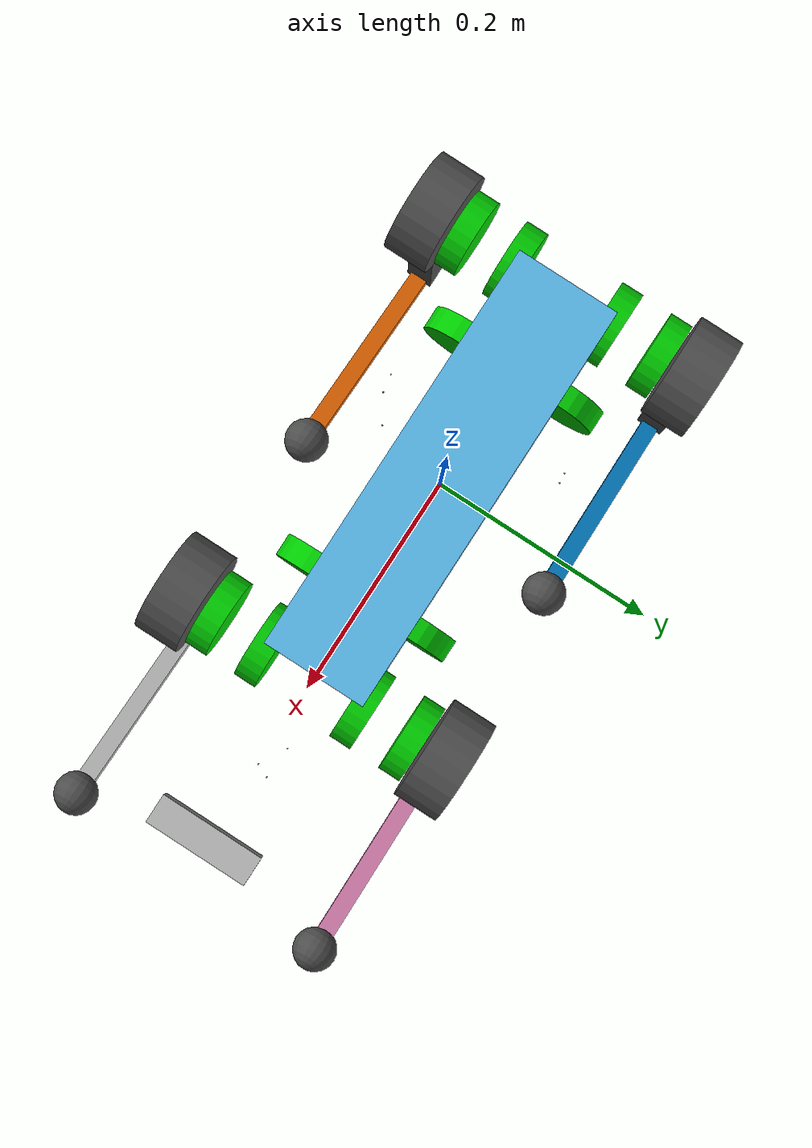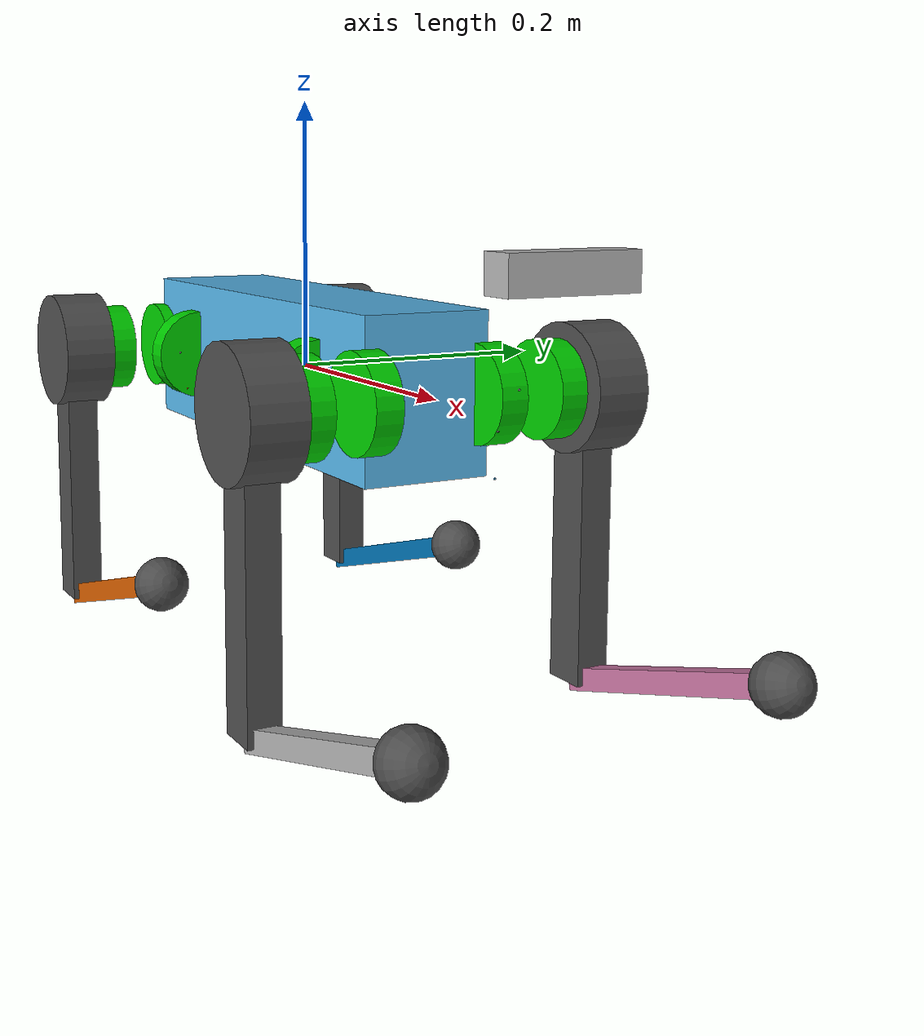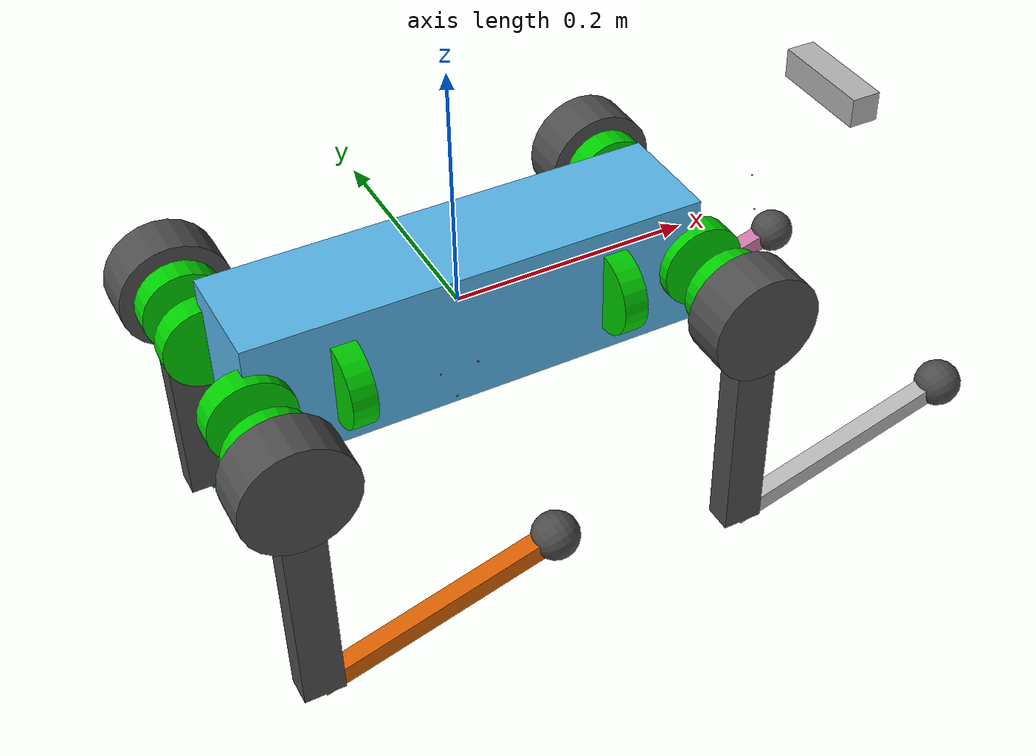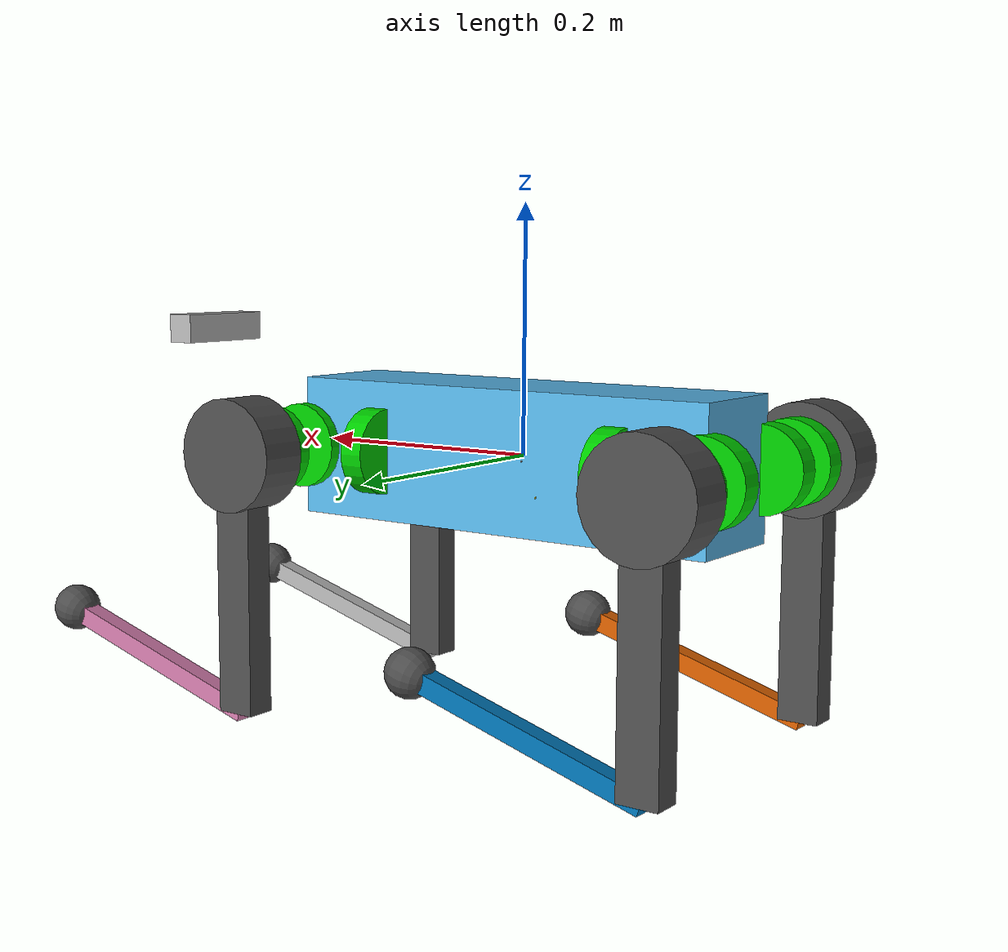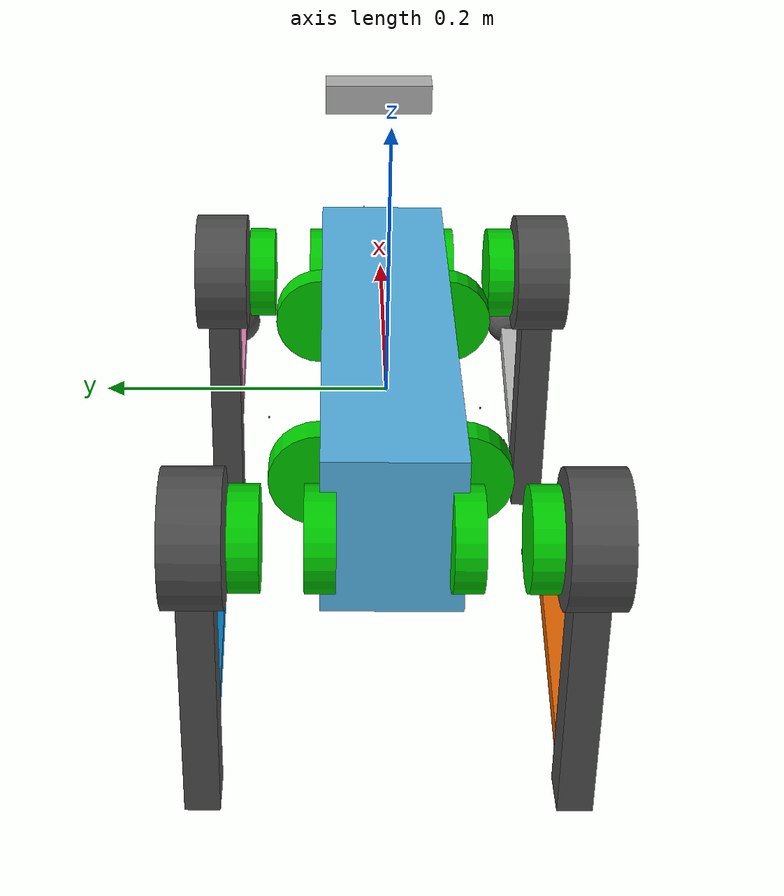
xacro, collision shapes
<?xml version="1.0"?>

<robot name="go1_description" xmlns:xacro="http://www.ros.org/wiki/xacro">

    <xacro:include filename="$(find go1_description)/urdf/go1.urdf"/>
    <xacro:include filename="$(find go1_description)/xacro/gazebo.xacro"/>
    <xacro:include filename="$(find realsense_ros_gazebo)/xacro/depthcam.xacro"/>

    <xacro:realsense_d435 sensor_name="d435" parent_link="base" rate="30">
        <origin rpy="0 0.0 0" xyz="0.34 0.0 0.08"/>
    </xacro:realsense_d435>
</robot>

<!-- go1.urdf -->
<!-- |    This document was autogenerated by xacro from robot.xacro                    | -->
<!-- |    EDITING THIS FILE BY HAND IS NOT RECOMMENDED                                 | -->
<robot name="go1">
  <material name="black">
    <color rgba="0.0 0.0 0.0 1.0"/>
  </material>
  <material name="blue">
    <color rgba="0.0 0.0 0.8 1.0"/>
  </material>
  <material name="green">
    <color rgba="0.0 0.8 0.0 1.0"/>
  </material>
  <material name="grey">
    <color rgba="0.2 0.2 0.2 1.0"/>
  </material>
  <material name="silver">
    <color rgba="0.9137254901960784 0.9137254901960784 0.8470588235294118 1.0"/>
  </material>
  <material name="orange">
    <color rgba="1.0 0.4235294117647059 0.0392156862745098 1.0"/>
  </material>
  <material name="brown">
    <color rgba="0.8705882352941177 0.8117647058823529 0.7647058823529411 1.0"/>
  </material>
  <material name="red">
    <color rgba="0.8 0.0 0.0 1.0"/>
  </material>
  <material name="white">
    <color rgba="1.0 1.0 1.0 1.0"/>
  </material>
  <!-- ros_control plugin -->
  <gazebo>
    <plugin filename="libgazebo_ros_control.so" name="gazebo_ros_control">
      <robotNamespace>/go1_gazebo</robotNamespace>
      <robotSimType>gazebo_ros_control/DefaultRobotHWSim</robotSimType>
    </plugin>
  </gazebo>
  <!-- Show the trajectory of trunk center. -->
  <gazebo>
    <plugin filename="libLinkPlot3DPlugin.so" name="3dplot">
      <frequency>10</frequency>
      <plot>
        <link>base</link>
        <pose>0 0 0 0 0 0</pose>
        <material>Gazebo/Yellow</material>
      </plot>
    </plugin>
  </gazebo>
  <!-- Show the trajectory of foot. You can add another trajectory about another foot. -->
  <gazebo>
    <plugin filename="libgazebo_ros_force.so" name="gazebo_ros_force">
      <bodyName>trunk</bodyName>
      <topicName>/apply_force/trunk</topicName>
    </plugin>
  </gazebo>
  <gazebo reference="imu_link">
    <gravity>true</gravity>
    <sensor name="imu_sensor" type="imu">
      <always_on>true</always_on>
      <update_rate>1000</update_rate>
      <visualize>true</visualize>
      <topic>__default_topic__</topic>
      <plugin filename="libgazebo_ros_imu_sensor.so" name="imu_plugin">
        <topicName>trunk_imu</topicName>
        <bodyName>imu_link</bodyName>
        <updateRateHZ>1000.0</updateRateHZ>
        <gaussianNoise>0.0</gaussianNoise>
        <xyzOffset>0 0 0</xyzOffset>
        <rpyOffset>0 0 0</rpyOffset>
        <frameName>imu_link</frameName>
      </plugin>
      <pose>0 0 0 0 0 0</pose>
    </sensor>
  </gazebo>
  <!-- Depth camera -->
  <gazebo reference="depthCamera_link_left">
    <sensor name="camera_link_camera" type="depth">
      <update_rate>20</update_rate>
      <camera>
        <horizontal_fov>1.047198</horizontal_fov>
        <image>
          <width>640</width>
          <height>480</height>
          <format>R8G8B8</format>
        </image>
        <clip>
          <near>0.05</near>
          <far>3</far>
        </clip>
      </camera>
      <plugin filename="libgazebo_ros_openni_kinect.so" name="camera_link_controller">
        <baseline>0.2</baseline>
        <alwaysOn>true</alwaysOn>
        <updateRate>1.0</updateRate>
        <cameraName>camera_link_ir</cameraName>
        <imageTopicName>/camera_link/color/image_raw</imageTopicName>
        <cameraInfoTopicName>/camera_link/color/camera_info</cameraInfoTopicName>
        <depthImageTopicName>/camera_link/depth/image_raw</depthImageTopicName>
        <depthImageInfoTopicName>/camera_link/depth/camera_info</depthImageInfoTopicName>
        <pointCloudTopicName>/camera_link/depth/points</pointCloudTopicName>
        <frameName>depthCamera_link_left</frameName>
        <pointCloudCutoff>0.5</pointCloudCutoff>
        <pointCloudCutoffMax>3.0</pointCloudCutoffMax>
        <distortionK1>0.00000001</distortionK1>
        <distortionK2>0.00000001</distortionK2>
        <distortionK3>0.00000001</distortionK3>
        <distortionT1>0.00000001</distortionT1>
        <distortionT2>0.00000001</distortionT2>
        <CxPrime>0</CxPrime>
        <Cx>0</Cx>
        <Cy>0</Cy>
        <focalLength>0</focalLength>
        <hackBaseline>0</hackBaseline>
      </plugin>
    </sensor>
  </gazebo>
  <!-- Foot contacts. -->
  <gazebo reference="FR_calf">
    <sensor name="FR_foot_contact" type="contact">
      <update_rate>100</update_rate>
      <plugin filename="libunitreeFootContactPlugin.so" name="contactPlugin"/>
      <contact>
        <collision>FR_calf_fixed_joint_lump__FR_foot_collision_1</collision>
      </contact>
    </sensor>
  </gazebo>
  <gazebo reference="FL_calf">
    <sensor name="FL_foot_contact" type="contact">
      <update_rate>100</update_rate>
      <plugin filename="libunitreeFootContactPlugin.so" name="contactPlugin"/>
      <contact>
        <collision>FL_calf_fixed_joint_lump__FL_foot_collision_1</collision>
      </contact>
    </sensor>
  </gazebo>
  <gazebo reference="RR_calf">
    <sensor name="RR_foot_contact" type="contact">
      <update_rate>100</update_rate>
      <plugin filename="libunitreeFootContactPlugin.so" name="contactPlugin"/>
      <contact>
        <collision>RR_calf_fixed_joint_lump__RR_foot_collision_1</collision>
      </contact>
    </sensor>
  </gazebo>
  <gazebo reference="RL_calf">
    <sensor name="RL_foot_contact" type="contact">
      <update_rate>100</update_rate>
      <plugin filename="libunitreeFootContactPlugin.so" name="contactPlugin"/>
      <contact>
        <collision>RL_calf_fixed_joint_lump__RL_foot_collision_1</collision>
      </contact>
    </sensor>
  </gazebo>
  <!-- Visualization of Foot contacts. -->
  <gazebo reference="FR_foot">
    <visual>
      <plugin filename="libunitreeDrawForcePlugin.so" name="drawForcePlugin">
        <topicName>FR_foot_contact</topicName>
      </plugin>
    </visual>
  </gazebo>
  <gazebo reference="FL_foot">
    <visual>
      <plugin filename="libunitreeDrawForcePlugin.so" name="drawForcePlugin">
        <topicName>FL_foot_contact</topicName>
      </plugin>
    </visual>
  </gazebo>
  <gazebo reference="RR_foot">
    <visual>
      <plugin filename="libunitreeDrawForcePlugin.so" name="drawForcePlugin">
        <topicName>RR_foot_contact</topicName>
      </plugin>
    </visual>
  </gazebo>
  <gazebo reference="RL_foot">
    <visual>
      <plugin filename="libunitreeDrawForcePlugin.so" name="drawForcePlugin">
        <topicName>RL_foot_contact</topicName>
      </plugin>
    </visual>
  </gazebo>
  <gazebo reference="base">
    <material>Gazebo/Green</material>
    <turnGravityOff>false</turnGravityOff>
  </gazebo>
  <gazebo reference="trunk">
    <mu1>0.2</mu1>
    <mu2>0.2</mu2>
    <kp value="1000000.0"/>
    <kd value="1.0"/>
  </gazebo>
  <gazebo reference="stick_link">
    <mu1>0.2</mu1>
    <mu2>0.2</mu2>
    <material>Gazebo/White</material>
  </gazebo>
  <gazebo reference="imu_link">
    <mu1>0.2</mu1>
    <mu2>0.2</mu2>
    <material>Gazebo/Red</material>
  </gazebo>
  <!-- FL leg -->
  <gazebo reference="FL_hip">
    <mu1>0.2</mu1>
    <mu2>0.2</mu2>
    <material>Gazebo/DarkGrey</material>
  </gazebo>
  <gazebo reference="FL_thigh">
    <mu1>0.2</mu1>
    <mu2>0.2</mu2>
    <self_collide>1</self_collide>
    <material>Gazebo/DarkGrey</material>
    <kp value="1000000.0"/>
    <kd value="1.0"/>
  </gazebo>
  <gazebo reference="FL_calf">
    <mu1>0.2</mu1>
    <mu2>0.2</mu2>
    <self_collide>1</self_collide>
  </gazebo>
  <gazebo reference="FL_foot">
    <mu1>0.6</mu1>
    <mu2>0.6</mu2>
    <self_collide>1</self_collide>
    <material>Gazebo/DarkGrey</material>
    <kp value="1000000.0"/>
    <kd value="1.0"/>
  </gazebo>
  <!-- FR leg -->
  <gazebo reference="FR_hip">
    <mu1>0.2</mu1>
    <mu2>0.2</mu2>
    <material>Gazebo/DarkGrey</material>
  </gazebo>
  <gazebo reference="FR_thigh">
    <mu1>0.2</mu1>
    <mu2>0.2</mu2>
    <self_collide>1</self_collide>
    <material>Gazebo/DarkGrey</material>
    <kp value="1000000.0"/>
    <kd value="1.0"/>
  </gazebo>
  <gazebo reference="FR_calf">
    <mu1>0.2</mu1>
    <mu2>0.2</mu2>
    <self_collide>1</self_collide>
  </gazebo>
  <gazebo reference="FR_foot">
    <mu1>0.6</mu1>
    <mu2>0.6</mu2>
    <self_collide>1</self_collide>
    <material>Gazebo/DarkGrey</material>
    <kp value="1000000.0"/>
    <kd value="1.0"/>
  </gazebo>
  <!-- RL leg -->
  <gazebo reference="RL_hip">
    <mu1>0.2</mu1>
    <mu2>0.2</mu2>
    <material>Gazebo/DarkGrey</material>
  </gazebo>
  <gazebo reference="RL_thigh">
    <mu1>0.2</mu1>
    <mu2>0.2</mu2>
    <self_collide>1</self_collide>
    <material>Gazebo/DarkGrey</material>
    <kp value="1000000.0"/>
    <kd value="1.0"/>
  </gazebo>
  <gazebo reference="RL_calf">
    <mu1>0.2</mu1>
    <mu2>0.2</mu2>
    <self_collide>1</self_collide>
  </gazebo>
  <gazebo reference="RL_foot">
    <mu1>0.6</mu1>
    <mu2>0.6</mu2>
    <self_collide>1</self_collide>
    <material>Gazebo/DarkGrey</material>
    <kp value="1000000.0"/>
    <kd value="1.0"/>
  </gazebo>
  <!-- RR leg -->
  <gazebo reference="RR_hip">
    <mu1>0.2</mu1>
    <mu2>0.2</mu2>
    <material>Gazebo/DarkGrey</material>
  </gazebo>
  <gazebo reference="RR_thigh">
    <mu1>0.2</mu1>
    <mu2>0.2</mu2>
    <self_collide>1</self_collide>
    <material>Gazebo/DarkGrey</material>
    <kp value="1000000.0"/>
    <kd value="1.0"/>
  </gazebo>
  <gazebo reference="RR_calf">
    <mu1>0.2</mu1>
    <mu2>0.2</mu2>
    <self_collide>1</self_collide>
  </gazebo>
  <gazebo reference="RR_foot">
    <mu1>0.6</mu1>
    <mu2>0.6</mu2>
    <self_collide>1</self_collide>
    <material>Gazebo/DarkGrey</material>
    <kp value="1000000.0"/>
    <kd value="1.0"/>
  </gazebo>
  <!-- Rotor related joint and link is only for demonstrate location. -->
  <!-- Actually, the rotor will rotate and the joint is not fixed. Reduction ratio should be considered. -->
  <!-- Debug mode will hung up the robot, use "true" or "false" to switch it. -->
  <link name="base">
    <visual>
      <origin rpy="0 0 0" xyz="0 0 0"/>
      <geometry>
        <box size="0.001 0.001 0.001"/>
      </geometry>
    </visual>
  </link>
  <joint name="floating_base" type="fixed">
    <origin rpy="0 0 0" xyz="0 0 0"/>
    <parent link="base"/>
    <child link="trunk"/>
  </joint>
  <link name="trunk">
    <visual>
      <origin rpy="0 0 0" xyz="0 0 0"/>
      <geometry>
        <mesh filename="package://go1_description/meshes/trunk.dae" scale="1 1 1"/>
      </geometry>
    </visual>
    <collision>
      <origin rpy="0 0 0" xyz="0 0 0"/>
      <geometry>
        <box size="0.3762 0.0935 0.114"/>
      </geometry>
    </collision>
    <inertial>
      <origin rpy="0 0 0" xyz="0.0223 0.002 -0.0005"/>
      <mass value="5.204"/>
      <inertia ixx="0.0168128557" ixy="-0.0002296769" ixz="-0.0002945293" iyy="0.063009565" iyz="-4.18731e-05" izz="0.0716547275"/>
    </inertial>
  </link>
  <joint name="imu_joint" type="fixed">
    <parent link="trunk"/>
    <child link="imu_link"/>
    <origin rpy="0 0 0" xyz="-0.01592 -0.06659 -0.00617"/>
  </joint>
  <link name="imu_link">
    <inertial>
      <mass value="0.001"/>
      <origin rpy="0 0 0" xyz="0 0 0"/>
      <inertia ixx="0.0001" ixy="0" ixz="0" iyy="0.0001" iyz="0" izz="0.0001"/>
    </inertial>
    <visual>
      <origin rpy="0 0 0" xyz="0 0 0"/>
      <geometry>
        <box size="0.001 0.001 0.001"/>
      </geometry>
    </visual>
    <collision>
      <origin rpy="0 0 0" xyz="0 0 0"/>
      <geometry>
        <box size=".001 .001 .001"/>
      </geometry>
    </collision>
  </link>
  <joint name="FR_hip_joint" type="revolute">
    <origin rpy="0 0 0" xyz="0.1881 -0.04675 0"/>
    <parent link="trunk"/>
    <child link="FR_hip"/>
    <axis xyz="1 0 0"/>
    <dynamics damping="0.0" friction="0.0"/>
    <limit effort="23.7" lower="-0.863" upper="0.863" velocity="30.1"/>
  </joint>
  <joint name="FR_hip_rotor_joint" type="fixed">
    <origin rpy="0 0 0" xyz="0.11215 -0.04675 0"/>
    <parent link="trunk"/>
    <child link="FR_hip_rotor"/>
  </joint>
  <link name="FR_hip">
    <visual>
      <origin rpy="3.141592653589793 0 0" xyz="0 0 0"/>
      <geometry>
        <mesh filename="package://go1_description/meshes/hip.dae" scale="1 1 1"/>
      </geometry>
    </visual>
    <collision>
      <origin rpy="1.5707963267948966 0 0" xyz="0 -0.08 0"/>
      <geometry>
        <cylinder length="0.04" radius="0.046"/>
      </geometry>
    </collision>
    <inertial>
      <origin rpy="0 0 0" xyz="-0.005657 0.008752 -0.000102"/>
      <mass value="0.591"/>
      <inertia ixx="0.000334008405" ixy="1.0826066e-05" ixz="1.290732e-06" iyy="0.000619101213" iyz="-1.643194e-06" izz="0.00040057614"/>
    </inertial>
  </link>
  <link name="FR_hip_rotor">
    <visual>
      <origin rpy="0 1.5707963267948966 0" xyz="0 0 0"/>
      <geometry>
        <cylinder length="0.02" radius="0.035"/>
      </geometry>
      <material name="green"/>
    </visual>
    <collision>
      <origin rpy="0 1.5707963267948966 0" xyz="0 0 0"/>
      <geometry>
        <cylinder length="0.02" radius="0.035"/>
      </geometry>
    </collision>
    <inertial>
      <origin rpy="0 0 0" xyz="0.0 0.0 0.0"/>
      <mass value="0.089"/>
      <inertia ixx="0.000111842" ixy="0.0" ixz="0.0" iyy="5.9647e-05" iyz="0.0" izz="5.9647e-05"/>
    </inertial>
  </link>
  <joint name="FR_thigh_joint" type="revolute">
    <origin rpy="0 0 0" xyz="0 -0.08 0"/>
    <parent link="FR_hip"/>
    <child link="FR_thigh"/>
    <axis xyz="0 1 0"/>
    <dynamics damping="0.0" friction="0.0"/>
    <limit effort="23.7" lower="-0.686" upper="4.501" velocity="30.1"/>
  </joint>
  <joint name="FR_thigh_rotor_joint" type="fixed">
    <origin rpy="0 0 0" xyz="0.0 0.00015 0"/>
    <parent link="FR_hip"/>
    <child link="FR_thigh_rotor"/>
  </joint>
  <link name="FR_thigh">
    <visual>
      <origin rpy="0 0 0" xyz="0 0 0"/>
      <geometry>
        <mesh filename="package://go1_description/meshes/thigh_mirror.dae" scale="1 1 1"/>
      </geometry>
    </visual>
    <collision>
      <origin rpy="0 1.5707963267948966 0" xyz="0 0 -0.1065"/>
      <geometry>
        <box size="0.213 0.0245 0.034"/>
      </geometry>
    </collision>
    <inertial>
      <origin rpy="0 0 0" xyz="-0.003342 0.018054 -0.033451"/>
      <mass value="0.92"/>
      <inertia ixx="0.004431760472" ixy="-5.7496807e-05" ixz="-0.000218457134" iyy="0.004485671726" iyz="-0.000572001265" izz="0.000740309489"/>
    </inertial>
  </link>
  <link name="FR_thigh_rotor">
    <visual>
      <origin rpy="1.5707963267948966 0 0" xyz="0 0 0"/>
      <geometry>
        <cylinder length="0.02" radius="0.035"/>
      </geometry>
      <material name="green"/>
    </visual>
    <collision>
      <origin rpy="1.5707963267948966 0 0" xyz="0 0 0"/>
      <geometry>
        <cylinder length="0.02" radius="0.035"/>
      </geometry>
    </collision>
    <inertial>
      <origin rpy="0 0 0" xyz="0.0 0.0 0.0"/>
      <mass value="0.089"/>
      <inertia ixx="5.9647e-05" ixy="0.0" ixz="0.0" iyy="0.000111842" iyz="0.0" izz="5.9647e-05"/>
    </inertial>
  </link>
  <joint name="FR_calf_joint" type="revolute">
    <origin rpy="0 0 0" xyz="0 0 -0.213"/>
    <parent link="FR_thigh"/>
    <child link="FR_calf"/>
    <axis xyz="0 1 0"/>
    <dynamics damping="0.0" friction="0.0"/>
    <limit effort="35.55" lower="-2.818" upper="-0.888" velocity="20.06"/>
  </joint>
  <joint name="FR_calf_rotor_joint" type="fixed">
    <origin rpy="0 0 0" xyz="0.0 0.03235 0"/>
    <parent link="FR_thigh"/>
    <child link="FR_calf_rotor"/>
  </joint>
  <link name="FR_calf">
    <visual>
      <origin rpy="0 0 0" xyz="0 0 0"/>
      <geometry>
        <mesh filename="package://go1_description/meshes/calf.dae" scale="1 1 1"/>
      </geometry>
    </visual>
    <collision>
      <origin rpy="0 1.5707963267948966 0" xyz="0 0 -0.1065"/>
      <geometry>
        <box size="0.213 0.016 0.016"/>
      </geometry>
    </collision>
    <inertial>
      <origin rpy="0 0 0" xyz="0.006197 0.001408 -0.116695"/>
      <mass value="0.135862"/>
      <inertia ixx="0.001088793059" ixy="-2.55679e-07" ixz="7.117814e-06" iyy="0.001100428748" iyz="2.077264e-06" izz="2.4787446e-05"/>
    </inertial>
  </link>
  <link name="FR_calf_rotor">
    <visual>
      <origin rpy="1.5707963267948966 0 0" xyz="0 0 0"/>
      <geometry>
        <cylinder length="0.02" radius="0.035"/>
      </geometry>
      <material name="green"/>
    </visual>
    <collision>
      <origin rpy="1.5707963267948966 0 0" xyz="0 0 0"/>
      <geometry>
        <cylinder length="0.02" radius="0.035"/>
      </geometry>
    </collision>
    <inertial>
      <origin rpy="0 0 0" xyz="0.0 0.0 0.0"/>
      <mass value="0.089"/>
      <inertia ixx="5.9647e-05" ixy="0.0" ixz="0.0" iyy="0.000111842" iyz="0.0" izz="5.9647e-05"/>
    </inertial>
  </link>
  <joint name="FR_foot_fixed" type="fixed">
    <origin rpy="0 0 0" xyz="0 0 -0.213"/>
    <parent link="FR_calf"/>
    <child link="FR_foot"/>
  </joint>
  <link name="FR_foot">
    <visual>
      <origin rpy="0 0 0" xyz="0 0 0"/>
      <geometry>
        <sphere radius="0.01"/>
      </geometry>
    </visual>
    <collision>
      <origin rpy="0 0 0" xyz="0 0 0"/>
      <geometry>
        <sphere radius="0.02"/>
      </geometry>
    </collision>
    <inertial>
      <mass value="0.06"/>
      <inertia ixx="9.600000000000001e-06" ixy="0.0" ixz="0.0" iyy="9.600000000000001e-06" iyz="0.0" izz="9.600000000000001e-06"/>
    </inertial>
  </link>
  <transmission name="FR_hip_tran">
    <type>transmission_interface/SimpleTransmission</type>
    <joint name="FR_hip_joint">
      <hardwareInterface>hardware_interface/EffortJointInterface</hardwareInterface>
    </joint>
    <actuator name="FR_hip_motor">
      <hardwareInterface>hardware_interface/EffortJointInterface</hardwareInterface>
      <mechanicalReduction>1</mechanicalReduction>
    </actuator>
  </transmission>
  <transmission name="FR_thigh_tran">
    <type>transmission_interface/SimpleTransmission</type>
    <joint name="FR_thigh_joint">
      <hardwareInterface>hardware_interface/EffortJointInterface</hardwareInterface>
    </joint>
    <actuator name="FR_thigh_motor">
      <hardwareInterface>hardware_interface/EffortJointInterface</hardwareInterface>
      <mechanicalReduction>1</mechanicalReduction>
    </actuator>
  </transmission>
  <transmission name="FR_calf_tran">
    <type>transmission_interface/SimpleTransmission</type>
    <joint name="FR_calf_joint">
      <hardwareInterface>hardware_interface/EffortJointInterface</hardwareInterface>
    </joint>
    <actuator name="FR_calf_motor">
      <hardwareInterface>hardware_interface/EffortJointInterface</hardwareInterface>
      <mechanicalReduction>1</mechanicalReduction>
    </actuator>
  </transmission>
  <joint name="FL_hip_joint" type="revolute">
    <origin rpy="0 0 0" xyz="0.1881 0.04675 0"/>
    <parent link="trunk"/>
    <child link="FL_hip"/>
    <axis xyz="1 0 0"/>
    <dynamics damping="0.0" friction="0.0"/>
    <limit effort="23.7" lower="-0.863" upper="0.863" velocity="30.1"/>
  </joint>
  <joint name="FL_hip_rotor_joint" type="fixed">
    <origin rpy="0 0 0" xyz="0.11215 0.04675 0"/>
    <parent link="trunk"/>
    <child link="FL_hip_rotor"/>
  </joint>
  <link name="FL_hip">
    <visual>
      <origin rpy="0 0 0" xyz="0 0 0"/>
      <geometry>
        <mesh filename="package://go1_description/meshes/hip.dae" scale="1 1 1"/>
      </geometry>
    </visual>
    <collision>
      <origin rpy="1.5707963267948966 0 0" xyz="0 0.08 0"/>
      <geometry>
        <cylinder length="0.04" radius="0.046"/>
      </geometry>
    </collision>
    <inertial>
      <origin rpy="0 0 0" xyz="-0.005657 -0.008752 -0.000102"/>
      <mass value="0.591"/>
      <inertia ixx="0.000334008405" ixy="-1.0826066e-05" ixz="1.290732e-06" iyy="0.000619101213" iyz="1.643194e-06" izz="0.00040057614"/>
    </inertial>
  </link>
  <link name="FL_hip_rotor">
    <visual>
      <origin rpy="0 1.5707963267948966 0" xyz="0 0 0"/>
      <geometry>
        <cylinder length="0.02" radius="0.035"/>
      </geometry>
      <material name="green"/>
    </visual>
    <collision>
      <origin rpy="0 1.5707963267948966 0" xyz="0 0 0"/>
      <geometry>
        <cylinder length="0.02" radius="0.035"/>
      </geometry>
    </collision>
    <inertial>
      <origin rpy="0 0 0" xyz="0.0 0.0 0.0"/>
      <mass value="0.089"/>
      <inertia ixx="0.000111842" ixy="0.0" ixz="0.0" iyy="5.9647e-05" iyz="0.0" izz="5.9647e-05"/>
    </inertial>
  </link>
  <joint name="FL_thigh_joint" type="revolute">
    <origin rpy="0 0 0" xyz="0 0.08 0"/>
    <parent link="FL_hip"/>
    <child link="FL_thigh"/>
    <axis xyz="0 1 0"/>
    <dynamics damping="0.0" friction="0.0"/>
    <limit effort="23.7" lower="-0.686" upper="4.501" velocity="30.1"/>
  </joint>
  <joint name="FL_thigh_rotor_joint" type="fixed">
    <origin rpy="0 0 0" xyz="0.0 -0.00015 0"/>
    <parent link="FL_hip"/>
    <child link="FL_thigh_rotor"/>
  </joint>
  <link name="FL_thigh">
    <visual>
      <origin rpy="0 0 0" xyz="0 0 0"/>
      <geometry>
        <mesh filename="package://go1_description/meshes/thigh.dae" scale="1 1 1"/>
      </geometry>
    </visual>
    <collision>
      <origin rpy="0 1.5707963267948966 0" xyz="0 0 -0.1065"/>
      <geometry>
        <box size="0.213 0.0245 0.034"/>
      </geometry>
    </collision>
    <inertial>
      <origin rpy="0 0 0" xyz="-0.003342 -0.018054 -0.033451"/>
      <mass value="0.92"/>
      <inertia ixx="0.004431760472" ixy="5.7496807e-05" ixz="-0.000218457134" iyy="0.004485671726" iyz="0.000572001265" izz="0.000740309489"/>
    </inertial>
  </link>
  <link name="FL_thigh_rotor">
    <visual>
      <origin rpy="1.5707963267948966 0 0" xyz="0 0 0"/>
      <geometry>
        <cylinder length="0.02" radius="0.035"/>
      </geometry>
      <material name="green"/>
    </visual>
    <collision>
      <origin rpy="1.5707963267948966 0 0" xyz="0 0 0"/>
      <geometry>
        <cylinder length="0.02" radius="0.035"/>
      </geometry>
    </collision>
    <inertial>
      <origin rpy="0 0 0" xyz="0.0 0.0 0.0"/>
      <mass value="0.089"/>
      <inertia ixx="5.9647e-05" ixy="0.0" ixz="0.0" iyy="0.000111842" iyz="0.0" izz="5.9647e-05"/>
    </inertial>
  </link>
  <joint name="FL_calf_joint" type="revolute">
    <origin rpy="0 0 0" xyz="0 0 -0.213"/>
    <parent link="FL_thigh"/>
    <child link="FL_calf"/>
    <axis xyz="0 1 0"/>
    <dynamics damping="0.0" friction="0.0"/>
    <limit effort="35.55" lower="-2.818" upper="-0.888" velocity="20.06"/>
  </joint>
  <joint name="FL_calf_rotor_joint" type="fixed">
    <origin rpy="0 0 0" xyz="0.0 -0.03235 0"/>
    <parent link="FL_thigh"/>
    <child link="FL_calf_rotor"/>
  </joint>
  <link name="FL_calf">
    <visual>
      <origin rpy="0 0 0" xyz="0 0 0"/>
      <geometry>
        <mesh filename="package://go1_description/meshes/calf.dae" scale="1 1 1"/>
      </geometry>
    </visual>
    <collision>
      <origin rpy="0 1.5707963267948966 0" xyz="0 0 -0.1065"/>
      <geometry>
        <box size="0.213 0.016 0.016"/>
      </geometry>
    </collision>
    <inertial>
      <origin rpy="0 0 0" xyz="0.006197 0.001408 -0.116695"/>
      <mass value="0.135862"/>
      <inertia ixx="0.001088793059" ixy="-2.55679e-07" ixz="7.117814e-06" iyy="0.001100428748" iyz="2.077264e-06" izz="2.4787446e-05"/>
    </inertial>
  </link>
  <link name="FL_calf_rotor">
    <visual>
      <origin rpy="1.5707963267948966 0 0" xyz="0 0 0"/>
      <geometry>
        <cylinder length="0.02" radius="0.035"/>
      </geometry>
      <material name="green"/>
    </visual>
    <collision>
      <origin rpy="1.5707963267948966 0 0" xyz="0 0 0"/>
      <geometry>
        <cylinder length="0.02" radius="0.035"/>
      </geometry>
    </collision>
    <inertial>
      <origin rpy="0 0 0" xyz="0.0 0.0 0.0"/>
      <mass value="0.089"/>
      <inertia ixx="5.9647e-05" ixy="0.0" ixz="0.0" iyy="0.000111842" iyz="0.0" izz="5.9647e-05"/>
    </inertial>
  </link>
  <joint name="FL_foot_fixed" type="fixed">
    <origin rpy="0 0 0" xyz="0 0 -0.213"/>
    <parent link="FL_calf"/>
    <child link="FL_foot"/>
  </joint>
  <link name="FL_foot">
    <visual>
      <origin rpy="0 0 0" xyz="0 0 0"/>
      <geometry>
        <sphere radius="0.01"/>
      </geometry>
    </visual>
    <collision>
      <origin rpy="0 0 0" xyz="0 0 0"/>
      <geometry>
        <sphere radius="0.02"/>
      </geometry>
    </collision>
    <inertial>
      <mass value="0.06"/>
      <inertia ixx="9.600000000000001e-06" ixy="0.0" ixz="0.0" iyy="9.600000000000001e-06" iyz="0.0" izz="9.600000000000001e-06"/>
    </inertial>
  </link>
  <transmission name="FL_hip_tran">
    <type>transmission_interface/SimpleTransmission</type>
    <joint name="FL_hip_joint">
      <hardwareInterface>hardware_interface/EffortJointInterface</hardwareInterface>
    </joint>
    <actuator name="FL_hip_motor">
      <hardwareInterface>hardware_interface/EffortJointInterface</hardwareInterface>
      <mechanicalReduction>1</mechanicalReduction>
    </actuator>
  </transmission>
  <transmission name="FL_thigh_tran">
    <type>transmission_interface/SimpleTransmission</type>
    <joint name="FL_thigh_joint">
      <hardwareInterface>hardware_interface/EffortJointInterface</hardwareInterface>
    </joint>
    <actuator name="FL_thigh_motor">
      <hardwareInterface>hardware_interface/EffortJointInterface</hardwareInterface>
      <mechanicalReduction>1</mechanicalReduction>
    </actuator>
  </transmission>
  <transmission name="FL_calf_tran">
    <type>transmission_interface/SimpleTransmission</type>
    <joint name="FL_calf_joint">
      <hardwareInterface>hardware_interface/EffortJointInterface</hardwareInterface>
    </joint>
    <actuator name="FL_calf_motor">
      <hardwareInterface>hardware_interface/EffortJointInterface</hardwareInterface>
      <mechanicalReduction>1</mechanicalReduction>
    </actuator>
  </transmission>
  <joint name="RR_hip_joint" type="revolute">
    <origin rpy="0 0 0" xyz="-0.1881 -0.04675 0"/>
    <parent link="trunk"/>
    <child link="RR_hip"/>
    <axis xyz="1 0 0"/>
    <dynamics damping="0.0" friction="0.0"/>
    <limit effort="23.7" lower="-0.863" upper="0.863" velocity="30.1"/>
  </joint>
  <joint name="RR_hip_rotor_joint" type="fixed">
    <origin rpy="0 0 0" xyz="-0.11215 -0.04675 0"/>
    <parent link="trunk"/>
    <child link="RR_hip_rotor"/>
  </joint>
  <link name="RR_hip">
    <visual>
      <origin rpy="3.141592653589793 3.141592653589793 0" xyz="0 0 0"/>
      <geometry>
        <mesh filename="package://go1_description/meshes/hip.dae" scale="1 1 1"/>
      </geometry>
    </visual>
    <collision>
      <origin rpy="1.5707963267948966 0 0" xyz="0 -0.08 0"/>
      <geometry>
        <cylinder length="0.04" radius="0.046"/>
      </geometry>
    </collision>
    <inertial>
      <origin rpy="0 0 0" xyz="0.005657 0.008752 -0.000102"/>
      <mass value="0.591"/>
      <inertia ixx="0.000334008405" ixy="-1.0826066e-05" ixz="-1.290732e-06" iyy="0.000619101213" iyz="-1.643194e-06" izz="0.00040057614"/>
    </inertial>
  </link>
  <link name="RR_hip_rotor">
    <visual>
      <origin rpy="0 1.5707963267948966 0" xyz="0 0 0"/>
      <geometry>
        <cylinder length="0.02" radius="0.035"/>
      </geometry>
      <material name="green"/>
    </visual>
    <collision>
      <origin rpy="0 1.5707963267948966 0" xyz="0 0 0"/>
      <geometry>
        <cylinder length="0.02" radius="0.035"/>
      </geometry>
    </collision>
    <inertial>
      <origin rpy="0 0 0" xyz="0.0 0.0 0.0"/>
      <mass value="0.089"/>
      <inertia ixx="0.000111842" ixy="0.0" ixz="0.0" iyy="5.9647e-05" iyz="0.0" izz="5.9647e-05"/>
    </inertial>
  </link>
  <joint name="RR_thigh_joint" type="revolute">
    <origin rpy="0 0 0" xyz="0 -0.08 0"/>
    <parent link="RR_hip"/>
    <child link="RR_thigh"/>
    <axis xyz="0 1 0"/>
    <dynamics damping="0.0" friction="0.0"/>
    <limit effort="23.7" lower="-0.686" upper="4.501" velocity="30.1"/>
  </joint>
  <joint name="RR_thigh_rotor_joint" type="fixed">
    <origin rpy="0 0 0" xyz="0.0 0.00015 0"/>
    <parent link="RR_hip"/>
    <child link="RR_thigh_rotor"/>
  </joint>
  <link name="RR_thigh">
    <visual>
      <origin rpy="0 0 0" xyz="0 0 0"/>
      <geometry>
        <mesh filename="package://go1_description/meshes/thigh_mirror.dae" scale="1 1 1"/>
      </geometry>
    </visual>
    <collision>
      <origin rpy="0 1.5707963267948966 0" xyz="0 0 -0.1065"/>
      <geometry>
        <box size="0.213 0.0245 0.034"/>
      </geometry>
    </collision>
    <inertial>
      <origin rpy="0 0 0" xyz="-0.003342 0.018054 -0.033451"/>
      <mass value="0.92"/>
      <inertia ixx="0.004431760472" ixy="-5.7496807e-05" ixz="-0.000218457134" iyy="0.004485671726" iyz="-0.000572001265" izz="0.000740309489"/>
    </inertial>
  </link>
  <link name="RR_thigh_rotor">
    <visual>
      <origin rpy="1.5707963267948966 0 0" xyz="0 0 0"/>
      <geometry>
        <cylinder length="0.02" radius="0.035"/>
      </geometry>
      <material name="green"/>
    </visual>
    <collision>
      <origin rpy="1.5707963267948966 0 0" xyz="0 0 0"/>
      <geometry>
        <cylinder length="0.02" radius="0.035"/>
      </geometry>
    </collision>
    <inertial>
      <origin rpy="0 0 0" xyz="0.0 0.0 0.0"/>
      <mass value="0.089"/>
      <inertia ixx="5.9647e-05" ixy="0.0" ixz="0.0" iyy="0.000111842" iyz="0.0" izz="5.9647e-05"/>
    </inertial>
  </link>
  <joint name="RR_calf_joint" type="revolute">
    <origin rpy="0 0 0" xyz="0 0 -0.213"/>
    <parent link="RR_thigh"/>
    <child link="RR_calf"/>
    <axis xyz="0 1 0"/>
    <dynamics damping="0.0" friction="0.0"/>
    <limit effort="35.55" lower="-2.818" upper="-0.888" velocity="20.06"/>
  </joint>
  <joint name="RR_calf_rotor_joint" type="fixed">
    <origin rpy="0 0 0" xyz="0.0 0.03235 0"/>
    <parent link="RR_thigh"/>
    <child link="RR_calf_rotor"/>
  </joint>
  <link name="RR_calf">
    <visual>
      <origin rpy="0 0 0" xyz="0 0 0"/>
      <geometry>
        <mesh filename="package://go1_description/meshes/calf.dae" scale="1 1 1"/>
      </geometry>
    </visual>
    <collision>
      <origin rpy="0 1.5707963267948966 0" xyz="0 0 -0.1065"/>
      <geometry>
        <box size="0.213 0.016 0.016"/>
      </geometry>
    </collision>
    <inertial>
      <origin rpy="0 0 0" xyz="0.006197 0.001408 -0.116695"/>
      <mass value="0.135862"/>
      <inertia ixx="0.001088793059" ixy="-2.55679e-07" ixz="7.117814e-06" iyy="0.001100428748" iyz="2.077264e-06" izz="2.4787446e-05"/>
    </inertial>
  </link>
  <link name="RR_calf_rotor">
    <visual>
      <origin rpy="1.5707963267948966 0 0" xyz="0 0 0"/>
      <geometry>
        <cylinder length="0.02" radius="0.035"/>
      </geometry>
      <material name="green"/>
    </visual>
    <collision>
      <origin rpy="1.5707963267948966 0 0" xyz="0 0 0"/>
      <geometry>
        <cylinder length="0.02" radius="0.035"/>
      </geometry>
    </collision>
    <inertial>
      <origin rpy="0 0 0" xyz="0.0 0.0 0.0"/>
      <mass value="0.089"/>
      <inertia ixx="5.9647e-05" ixy="0.0" ixz="0.0" iyy="0.000111842" iyz="0.0" izz="5.9647e-05"/>
    </inertial>
  </link>
  <joint name="RR_foot_fixed" type="fixed">
    <origin rpy="0 0 0" xyz="0 0 -0.213"/>
    <parent link="RR_calf"/>
    <child link="RR_foot"/>
  </joint>
  <link name="RR_foot">
    <visual>
      <origin rpy="0 0 0" xyz="0 0 0"/>
      <geometry>
        <sphere radius="0.01"/>
      </geometry>
    </visual>
    <collision>
      <origin rpy="0 0 0" xyz="0 0 0"/>
      <geometry>
        <sphere radius="0.02"/>
      </geometry>
    </collision>
    <inertial>
      <mass value="0.06"/>
      <inertia ixx="9.600000000000001e-06" ixy="0.0" ixz="0.0" iyy="9.600000000000001e-06" iyz="0.0" izz="9.600000000000001e-06"/>
    </inertial>
  </link>
  <transmission name="RR_hip_tran">
    <type>transmission_interface/SimpleTransmission</type>
    <joint name="RR_hip_joint">
      <hardwareInterface>hardware_interface/EffortJointInterface</hardwareInterface>
    </joint>
    <actuator name="RR_hip_motor">
      <hardwareInterface>hardware_interface/EffortJointInterface</hardwareInterface>
      <mechanicalReduction>1</mechanicalReduction>
    </actuator>
  </transmission>
  <transmission name="RR_thigh_tran">
    <type>transmission_interface/SimpleTransmission</type>
    <joint name="RR_thigh_joint">
      <hardwareInterface>hardware_interface/EffortJointInterface</hardwareInterface>
    </joint>
    <actuator name="RR_thigh_motor">
      <hardwareInterface>hardware_interface/EffortJointInterface</hardwareInterface>
      <mechanicalReduction>1</mechanicalReduction>
    </actuator>
  </transmission>
  <transmission name="RR_calf_tran">
    <type>transmission_interface/SimpleTransmission</type>
    <joint name="RR_calf_joint">
      <hardwareInterface>hardware_interface/EffortJointInterface</hardwareInterface>
    </joint>
    <actuator name="RR_calf_motor">
      <hardwareInterface>hardware_interface/EffortJointInterface</hardwareInterface>
      <mechanicalReduction>1</mechanicalReduction>
    </actuator>
  </transmission>
  <joint name="RL_hip_joint" type="revolute">
    <origin rpy="0 0 0" xyz="-0.1881 0.04675 0"/>
    <parent link="trunk"/>
    <child link="RL_hip"/>
    <axis xyz="1 0 0"/>
    <dynamics damping="0.0" friction="0.0"/>
    <limit effort="23.7" lower="-0.863" upper="0.863" velocity="30.1"/>
  </joint>
  <joint name="RL_hip_rotor_joint" type="fixed">
    <origin rpy="0 0 0" xyz="-0.11215 0.04675 0"/>
    <parent link="trunk"/>
    <child link="RL_hip_rotor"/>
  </joint>
  <link name="RL_hip">
    <visual>
      <origin rpy="0 3.141592653589793 0" xyz="0 0 0"/>
      <geometry>
        <mesh filename="package://go1_description/meshes/hip.dae" scale="1 1 1"/>
      </geometry>
    </visual>
    <collision>
      <origin rpy="1.5707963267948966 0 0" xyz="0 0.08 0"/>
      <geometry>
        <cylinder length="0.04" radius="0.046"/>
      </geometry>
    </collision>
    <inertial>
      <origin rpy="0 0 0" xyz="0.005657 -0.008752 -0.000102"/>
      <mass value="0.591"/>
      <inertia ixx="0.000334008405" ixy="1.0826066e-05" ixz="-1.290732e-06" iyy="0.000619101213" iyz="1.643194e-06" izz="0.00040057614"/>
    </inertial>
  </link>
  <link name="RL_hip_rotor">
    <visual>
      <origin rpy="0 1.5707963267948966 0" xyz="0 0 0"/>
      <geometry>
        <cylinder length="0.02" radius="0.035"/>
      </geometry>
      <material name="green"/>
    </visual>
    <collision>
      <origin rpy="0 1.5707963267948966 0" xyz="0 0 0"/>
      <geometry>
        <cylinder length="0.02" radius="0.035"/>
      </geometry>
    </collision>
    <inertial>
      <origin rpy="0 0 0" xyz="0.0 0.0 0.0"/>
      <mass value="0.089"/>
      <inertia ixx="0.000111842" ixy="0.0" ixz="0.0" iyy="5.9647e-05" iyz="0.0" izz="5.9647e-05"/>
    </inertial>
  </link>
  <joint name="RL_thigh_joint" type="revolute">
    <origin rpy="0 0 0" xyz="0 0.08 0"/>
    <parent link="RL_hip"/>
    <child link="RL_thigh"/>
    <axis xyz="0 1 0"/>
    <dynamics damping="0.0" friction="0.0"/>
    <limit effort="23.7" lower="-0.686" upper="4.501" velocity="30.1"/>
  </joint>
  <joint name="RL_thigh_rotor_joint" type="fixed">
    <origin rpy="0 0 0" xyz="0.0 -0.00015 0"/>
    <parent link="RL_hip"/>
    <child link="RL_thigh_rotor"/>
  </joint>
  <link name="RL_thigh">
    <visual>
      <origin rpy="0 0 0" xyz="0 0 0"/>
      <geometry>
        <mesh filename="package://go1_description/meshes/thigh.dae" scale="1 1 1"/>
      </geometry>
    </visual>
    <collision>
      <origin rpy="0 1.5707963267948966 0" xyz="0 0 -0.1065"/>
      <geometry>
        <box size="0.213 0.0245 0.034"/>
      </geometry>
    </collision>
    <inertial>
      <origin rpy="0 0 0" xyz="-0.003342 -0.018054 -0.033451"/>
      <mass value="0.92"/>
      <inertia ixx="0.004431760472" ixy="5.7496807e-05" ixz="-0.000218457134" iyy="0.004485671726" iyz="0.000572001265" izz="0.000740309489"/>
    </inertial>
  </link>
  <link name="RL_thigh_rotor">
    <visual>
      <origin rpy="1.5707963267948966 0 0" xyz="0 0 0"/>
      <geometry>
        <cylinder length="0.02" radius="0.035"/>
      </geometry>
      <material name="green"/>
    </visual>
    <collision>
      <origin rpy="1.5707963267948966 0 0" xyz="0 0 0"/>
      <geometry>
        <cylinder length="0.02" radius="0.035"/>
      </geometry>
    </collision>
    <inertial>
      <origin rpy="0 0 0" xyz="0.0 0.0 0.0"/>
      <mass value="0.089"/>
      <inertia ixx="5.9647e-05" ixy="0.0" ixz="0.0" iyy="0.000111842" iyz="0.0" izz="5.9647e-05"/>
    </inertial>
  </link>
  <joint name="RL_calf_joint" type="revolute">
    <origin rpy="0 0 0" xyz="0 0 -0.213"/>
    <parent link="RL_thigh"/>
    <child link="RL_calf"/>
    <axis xyz="0 1 0"/>
    <dynamics damping="0.0" friction="0.0"/>
    <limit effort="35.55" lower="-2.818" upper="-0.888" velocity="20.06"/>
  </joint>
  <joint name="RL_calf_rotor_joint" type="fixed">
    <origin rpy="0 0 0" xyz="0.0 -0.03235 0"/>
    <parent link="RL_thigh"/>
    <child link="RL_calf_rotor"/>
  </joint>
  <link name="RL_calf">
    <visual>
      <origin rpy="0 0 0" xyz="0 0 0"/>
      <geometry>
        <mesh filename="package://go1_description/meshes/calf.dae" scale="1 1 1"/>
      </geometry>
    </visual>
    <collision>
      <origin rpy="0 1.5707963267948966 0" xyz="0 0 -0.1065"/>
      <geometry>
        <box size="0.213 0.016 0.016"/>
      </geometry>
    </collision>
    <inertial>
      <origin rpy="0 0 0" xyz="0.006197 0.001408 -0.116695"/>
      <mass value="0.135862"/>
      <inertia ixx="0.001088793059" ixy="-2.55679e-07" ixz="7.117814e-06" iyy="0.001100428748" iyz="2.077264e-06" izz="2.4787446e-05"/>
    </inertial>
  </link>
  <link name="RL_calf_rotor">
    <visual>
      <origin rpy="1.5707963267948966 0 0" xyz="0 0 0"/>
      <geometry>
        <cylinder length="0.02" radius="0.035"/>
      </geometry>
      <material name="green"/>
    </visual>
    <collision>
      <origin rpy="1.5707963267948966 0 0" xyz="0 0 0"/>
      <geometry>
        <cylinder length="0.02" radius="0.035"/>
      </geometry>
    </collision>
    <inertial>
      <origin rpy="0 0 0" xyz="0.0 0.0 0.0"/>
      <mass value="0.089"/>
      <inertia ixx="5.9647e-05" ixy="0.0" ixz="0.0" iyy="0.000111842" iyz="0.0" izz="5.9647e-05"/>
    </inertial>
  </link>
  <joint name="RL_foot_fixed" type="fixed">
    <origin rpy="0 0 0" xyz="0 0 -0.213"/>
    <parent link="RL_calf"/>
    <child link="RL_foot"/>
  </joint>
  <link name="RL_foot">
    <visual>
      <origin rpy="0 0 0" xyz="0 0 0"/>
      <geometry>
        <sphere radius="0.01"/>
      </geometry>
    </visual>
    <collision>
      <origin rpy="0 0 0" xyz="0 0 0"/>
      <geometry>
        <sphere radius="0.02"/>
      </geometry>
    </collision>
    <inertial>
      <mass value="0.06"/>
      <inertia ixx="9.600000000000001e-06" ixy="0.0" ixz="0.0" iyy="9.600000000000001e-06" iyz="0.0" izz="9.600000000000001e-06"/>
    </inertial>
  </link>
  <transmission name="RL_hip_tran">
    <type>transmission_interface/SimpleTransmission</type>
    <joint name="RL_hip_joint">
      <hardwareInterface>hardware_interface/EffortJointInterface</hardwareInterface>
    </joint>
    <actuator name="RL_hip_motor">
      <hardwareInterface>hardware_interface/EffortJointInterface</hardwareInterface>
      <mechanicalReduction>1</mechanicalReduction>
    </actuator>
  </transmission>
  <transmission name="RL_thigh_tran">
    <type>transmission_interface/SimpleTransmission</type>
    <joint name="RL_thigh_joint">
      <hardwareInterface>hardware_interface/EffortJointInterface</hardwareInterface>
    </joint>
    <actuator name="RL_thigh_motor">
      <hardwareInterface>hardware_interface/EffortJointInterface</hardwareInterface>
      <mechanicalReduction>1</mechanicalReduction>
    </actuator>
  </transmission>
  <transmission name="RL_calf_tran">
    <type>transmission_interface/SimpleTransmission</type>
    <joint name="RL_calf_joint">
      <hardwareInterface>hardware_interface/EffortJointInterface</hardwareInterface>
    </joint>
    <actuator name="RL_calf_motor">
      <hardwareInterface>hardware_interface/EffortJointInterface</hardwareInterface>
      <mechanicalReduction>1</mechanicalReduction>
    </actuator>
  </transmission>
  <joint name="camera_joint_face" type="fixed">
    <origin rpy="3.141592653589793 0 0" xyz="0.2785 0.0125 0.0167"/>
    <parent link="trunk"/>
    <child link="camera_face"/>
  </joint>
  <link name="camera_face">
    <collision>
      <origin rpy="0 0 0" xyz="0 0 0"/>
      <geometry>
        <box size=".001 .001 .001"/>
      </geometry>
    </collision>
    <visual>
      <origin rpy="0 0 0" xyz="0 0 0"/>
      <geometry>
        <mesh filename="package://go1_description/meshes/depthCamera.dae" scale="1 1 1"/>
      </geometry>
    </visual>
    <inertial>
      <mass value="1e-5"/>
      <origin rpy="0 0 0" xyz="0 0 0"/>
      <inertia ixx="1e-6" ixy="0" ixz="0" iyy="1e-6" iyz="0" izz="1e-6"/>
    </inertial>
  </link>
  <joint name="camera_optical_joint_face" type="fixed">
    <origin rpy="-1.5707963267948966 0 -1.5707963267948966" xyz="0 0 0"/>
    <parent link="camera_face"/>
    <child link="camera_optical_face"/>
  </joint>
  <link name="camera_optical_face">
        </link>
  <gazebo reference="camera_face">
    <sensor name="camera_face_camera" type="depth">
      <update_rate>16</update_rate>
      <camera>
        <horizontal_fov>2.094</horizontal_fov>
        <image>
          <width>928</width>
          <height>800</height>
          <format>R8G8B8</format>
        </image>
        <clip>
          <near>0.1</near>
          <far>5</far>
        </clip>
      </camera>
      <plugin filename="libgazebo_ros_openni_kinect.so" name="camera_face_controller">
        <baseline>0.025</baseline>
        <alwaysOn>true</alwaysOn>
        <updateRate>0.0</updateRate>
        <cameraName>camera_face_ir</cameraName>
        <imageTopicName>/camera_face/color/image_raw</imageTopicName>
        <cameraInfoTopicName>/camera_face/color/camera_info</cameraInfoTopicName>
        <depthImageTopicName>/camera_face/depth/image_raw</depthImageTopicName>
        <depthImageInfoTopicName>/camera_face/depth/camera_info</depthImageInfoTopicName>
        <pointCloudTopicName>/cam1/point_cloud_face</pointCloudTopicName>
        <frameName>camera_optical_face</frameName>
        <pointCloudCutoff>0.1</pointCloudCutoff>
        <pointCloudCutoffMax>1.5</pointCloudCutoffMax>
        <distortionK1>0.0</distortionK1>
        <distortionK2>0.0</distortionK2>
        <distortionK3>0.0</distortionK3>
        <distortionT1>0.0</distortionT1>
        <distortionT2>0.0</distortionT2>
        <CxPrime>0</CxPrime>
        <Cx>0.0045</Cx>
        <Cy>0.0039</Cy>
        <focalLength>0</focalLength>
        <hackBaseline>0</hackBaseline>
      </plugin>
    </sensor>
  </gazebo>
  <joint name="camera_joint_chin" type="fixed">
    <origin rpy="3.141592653589793 1.5707963267948966 0" xyz="0.2522 0.0125 -0.0436"/>
    <parent link="trunk"/>
    <child link="camera_chin"/>
  </joint>
  <link name="camera_chin">
    <collision>
      <origin rpy="0 0 0" xyz="0 0 0"/>
      <geometry>
        <box size=".001 .001 .001"/>
      </geometry>
    </collision>
    <visual>
      <origin rpy="0 0 0" xyz="0 0 0"/>
      <geometry>
        <mesh filename="package://go1_description/meshes/depthCamera.dae" scale="1 1 1"/>
      </geometry>
    </visual>
    <inertial>
      <mass value="1e-5"/>
      <origin rpy="0 0 0" xyz="0 0 0"/>
      <inertia ixx="1e-6" ixy="0" ixz="0" iyy="1e-6" iyz="0" izz="1e-6"/>
    </inertial>
  </link>
  <joint name="camera_optical_joint_chin" type="fixed">
    <origin rpy="-1.5707963267948966 0 -1.5707963267948966" xyz="0 0 0"/>
    <parent link="camera_chin"/>
    <child link="camera_optical_chin"/>
  </joint>
  <link name="camera_optical_chin">
        </link>
  <gazebo reference="camera_chin">
    <sensor name="camera_chin_camera" type="depth">
      <update_rate>16</update_rate>
      <camera>
        <horizontal_fov>2.094</horizontal_fov>
        <image>
          <width>928</width>
          <height>800</height>
          <format>R8G8B8</format>
        </image>
        <clip>
          <near>0.1</near>
          <far>5</far>
        </clip>
      </camera>
      <plugin filename="libgazebo_ros_openni_kinect.so" name="camera_chin_controller">
        <baseline>0.025</baseline>
        <alwaysOn>true</alwaysOn>
        <updateRate>0.0</updateRate>
        <cameraName>camera_chin_ir</cameraName>
        <imageTopicName>/camera_chin/color/image_raw</imageTopicName>
        <cameraInfoTopicName>/camera_chin/color/camera_info</cameraInfoTopicName>
        <depthImageTopicName>/camera_chin/depth/image_raw</depthImageTopicName>
        <depthImageInfoTopicName>/camera_chin/depth/camera_info</depthImageInfoTopicName>
        <pointCloudTopicName>/cam2/point_cloud_chin</pointCloudTopicName>
        <frameName>camera_optical_chin</frameName>
        <pointCloudCutoff>0.1</pointCloudCutoff>
        <pointCloudCutoffMax>1.5</pointCloudCutoffMax>
        <distortionK1>0.0</distortionK1>
        <distortionK2>0.0</distortionK2>
        <distortionK3>0.0</distortionK3>
        <distortionT1>0.0</distortionT1>
        <distortionT2>0.0</distortionT2>
        <CxPrime>0</CxPrime>
        <Cx>0.0045</Cx>
        <Cy>0.0039</Cy>
        <focalLength>0</focalLength>
        <hackBaseline>0</hackBaseline>
      </plugin>
    </sensor>
  </gazebo>
  <joint name="camera_joint_left" type="fixed">
    <origin rpy="3.141592653589793 0.2618 1.5707963267948966" xyz="-0.066 0.082 -0.0176"/>
    <parent link="trunk"/>
    <child link="camera_left"/>
  </joint>
  <link name="camera_left">
    <collision>
      <origin rpy="0 0 0" xyz="0 0 0"/>
      <geometry>
        <box size=".001 .001 .001"/>
      </geometry>
    </collision>
    <visual>
      <origin rpy="0 0 0" xyz="0 0 0"/>
      <geometry>
        <mesh filename="package://go1_description/meshes/depthCamera.dae" scale="1 1 1"/>
      </geometry>
    </visual>
    <inertial>
      <mass value="1e-5"/>
      <origin rpy="0 0 0" xyz="0 0 0"/>
      <inertia ixx="1e-6" ixy="0" ixz="0" iyy="1e-6" iyz="0" izz="1e-6"/>
    </inertial>
  </link>
  <joint name="camera_optical_joint_left" type="fixed">
    <origin rpy="-1.5707963267948966 0 -1.5707963267948966" xyz="0 0 0"/>
    <parent link="camera_left"/>
    <child link="camera_optical_left"/>
  </joint>
  <link name="camera_optical_left">
        </link>
  <gazebo reference="camera_left">
    <sensor name="camera_left_camera" type="depth">
      <update_rate>16</update_rate>
      <camera>
        <horizontal_fov>2.094</horizontal_fov>
        <image>
          <width>928</width>
          <height>800</height>
          <format>R8G8B8</format>
        </image>
        <clip>
          <near>0.1</near>
          <far>5</far>
        </clip>
      </camera>
      <plugin filename="libgazebo_ros_openni_kinect.so" name="camera_left_controller">
        <baseline>0.025</baseline>
        <alwaysOn>true</alwaysOn>
        <updateRate>0.0</updateRate>
        <cameraName>camera_left_ir</cameraName>
        <imageTopicName>/camera_left/color/image_raw</imageTopicName>
        <cameraInfoTopicName>/camera_left/color/camera_info</cameraInfoTopicName>
        <depthImageTopicName>/camera_left/depth/image_raw</depthImageTopicName>
        <depthImageInfoTopicName>/camera_left/depth/camera_info</depthImageInfoTopicName>
        <pointCloudTopicName>/cam3/point_cloud_left</pointCloudTopicName>
        <frameName>camera_optical_left</frameName>
        <pointCloudCutoff>0.1</pointCloudCutoff>
        <pointCloudCutoffMax>1.5</pointCloudCutoffMax>
        <distortionK1>0.0</distortionK1>
        <distortionK2>0.0</distortionK2>
        <distortionK3>0.0</distortionK3>
        <distortionT1>0.0</distortionT1>
        <distortionT2>0.0</distortionT2>
        <CxPrime>0</CxPrime>
        <Cx>0.0045</Cx>
        <Cy>0.0039</Cy>
        <focalLength>0</focalLength>
        <hackBaseline>0</hackBaseline>
      </plugin>
    </sensor>
  </gazebo>
  <joint name="camera_joint_right" type="fixed">
    <origin rpy="3.141592653589793 0.2618 -1.5707963267948966" xyz="-0.041 -0.082 -0.0176"/>
    <parent link="trunk"/>
    <child link="camera_right"/>
  </joint>
  <link name="camera_right">
    <collision>
      <origin rpy="0 0 0" xyz="0 0 0"/>
      <geometry>
        <box size=".001 .001 .001"/>
      </geometry>
    </collision>
    <visual>
      <origin rpy="0 0 0" xyz="0 0 0"/>
      <geometry>
        <mesh filename="package://go1_description/meshes/depthCamera.dae" scale="1 1 1"/>
      </geometry>
    </visual>
    <inertial>
      <mass value="1e-5"/>
      <origin rpy="0 0 0" xyz="0 0 0"/>
      <inertia ixx="1e-6" ixy="0" ixz="0" iyy="1e-6" iyz="0" izz="1e-6"/>
    </inertial>
  </link>
  <joint name="camera_optical_joint_right" type="fixed">
    <origin rpy="-1.5707963267948966 0 -1.5707963267948966" xyz="0 0 0"/>
    <parent link="camera_right"/>
    <child link="camera_optical_right"/>
  </joint>
  <link name="camera_optical_right">
        </link>
  <gazebo reference="camera_right">
    <sensor name="camera_right_camera" type="depth">
      <update_rate>16</update_rate>
      <camera>
        <horizontal_fov>2.094</horizontal_fov>
        <image>
          <width>928</width>
          <height>800</height>
          <format>R8G8B8</format>
        </image>
        <clip>
          <near>0.1</near>
          <far>5</far>
        </clip>
      </camera>
      <plugin filename="libgazebo_ros_openni_kinect.so" name="camera_right_controller">
        <baseline>0.025</baseline>
        <alwaysOn>true</alwaysOn>
        <updateRate>0.0</updateRate>
        <cameraName>camera_right_ir</cameraName>
        <imageTopicName>/camera_right/color/image_raw</imageTopicName>
        <cameraInfoTopicName>/camera_right/color/camera_info</cameraInfoTopicName>
        <depthImageTopicName>/camera_right/depth/image_raw</depthImageTopicName>
        <depthImageInfoTopicName>/camera_right/depth/camera_info</depthImageInfoTopicName>
        <pointCloudTopicName>/cam4/point_cloud_right</pointCloudTopicName>
        <frameName>camera_optical_right</frameName>
        <pointCloudCutoff>0.1</pointCloudCutoff>
        <pointCloudCutoffMax>1.5</pointCloudCutoffMax>
        <distortionK1>0.0</distortionK1>
        <distortionK2>0.0</distortionK2>
        <distortionK3>0.0</distortionK3>
        <distortionT1>0.0</distortionT1>
        <distortionT2>0.0</distortionT2>
        <CxPrime>0</CxPrime>
        <Cx>0.0045</Cx>
        <Cy>0.0039</Cy>
        <focalLength>0</focalLength>
        <hackBaseline>0</hackBaseline>
      </plugin>
    </sensor>
  </gazebo>
  <joint name="camera_joint_rearDown" type="fixed">
    <origin rpy="3.141592653589793 1.5707963267948966 0" xyz="-0.0825 0.0125 -0.04365"/>
    <parent link="trunk"/>
    <child link="camera_rearDown"/>
  </joint>
  <link name="camera_rearDown">
    <collision>
      <origin rpy="0 0 0" xyz="0 0 0"/>
      <geometry>
        <box size=".001 .001 .001"/>
      </geometry>
    </collision>
    <visual>
      <origin rpy="0 0 0" xyz="0 0 0"/>
      <geometry>
        <mesh filename="package://go1_description/meshes/depthCamera.dae" scale="1 1 1"/>
      </geometry>
    </visual>
    <inertial>
      <mass value="1e-5"/>
      <origin rpy="0 0 0" xyz="0 0 0"/>
      <inertia ixx="1e-6" ixy="0" ixz="0" iyy="1e-6" iyz="0" izz="1e-6"/>
    </inertial>
  </link>
  <joint name="camera_optical_joint_rearDown" type="fixed">
    <origin rpy="-1.5707963267948966 0 -1.5707963267948966" xyz="0 0 0"/>
    <parent link="camera_rearDown"/>
    <child link="camera_optical_rearDown"/>
  </joint>
  <link name="camera_optical_rearDown">
        </link>
  <gazebo reference="camera_rearDown">
    <sensor name="camera_rearDown_camera" type="depth">
      <update_rate>16</update_rate>
      <camera>
        <horizontal_fov>2.094</horizontal_fov>
        <image>
          <width>928</width>
          <height>800</height>
          <format>R8G8B8</format>
        </image>
        <clip>
          <near>0.1</near>
          <far>5</far>
        </clip>
      </camera>
      <plugin filename="libgazebo_ros_openni_kinect.so" name="camera_rearDown_controller">
        <baseline>0.025</baseline>
        <alwaysOn>true</alwaysOn>
        <updateRate>0.0</updateRate>
        <cameraName>camera_rearDown_ir</cameraName>
        <imageTopicName>/camera_rearDown/color/image_raw</imageTopicName>
        <cameraInfoTopicName>/camera_rearDown/color/camera_info</cameraInfoTopicName>
        <depthImageTopicName>/camera_rearDown/depth/image_raw</depthImageTopicName>
        <depthImageInfoTopicName>/camera_rearDown/depth/camera_info</depthImageInfoTopicName>
        <pointCloudTopicName>/cam5/point_cloud_rearDown</pointCloudTopicName>
        <frameName>camera_optical_rearDown</frameName>
        <pointCloudCutoff>0.1</pointCloudCutoff>
        <pointCloudCutoffMax>1.5</pointCloudCutoffMax>
        <distortionK1>0.0</distortionK1>
        <distortionK2>0.0</distortionK2>
        <distortionK3>0.0</distortionK3>
        <distortionT1>0.0</distortionT1>
        <distortionT2>0.0</distortionT2>
        <CxPrime>0</CxPrime>
        <Cx>0.0045</Cx>
        <Cy>0.0039</Cy>
        <focalLength>0</focalLength>
        <hackBaseline>0</hackBaseline>
      </plugin>
    </sensor>
  </gazebo>
  <joint name="camera_laserscan_joint_left" type="fixed">
    <origin rpy="0 0.2618 0" xyz="0 0 0"/>
    <parent link="camera_left"/>
    <child link="camera_laserscan_link_left"/>
  </joint>
  <link name="camera_laserscan_link_left">
    </link>
  <joint name="camera_laserscan_joint_right" type="fixed">
    <origin rpy="0 0.2618 0" xyz="0 0 0"/>
    <parent link="camera_right"/>
    <child link="camera_laserscan_link_right"/>
  </joint>
  <link name="camera_laserscan_link_right">
    </link>
  <joint name="ultraSound_joint_left" type="fixed">
    <origin rpy="0 0.2618 1.5707963267948966" xyz="-0.0535  0.0826 0.00868"/>
    <parent link="trunk"/>
    <child link="ultraSound_left"/>
  </joint>
  <link name="ultraSound_left">
    <collision>
      <origin rpy="0 0 0" xyz="0 0 0"/>
      <geometry>
        <box size=".001 .001 .001"/>
      </geometry>
    </collision>
    <visual>
      <origin rpy="0 0 0" xyz="0 0 0"/>
      <geometry>
        <mesh filename="package://go1_description/meshes/ultraSound.dae" scale="1 1 1"/>
      </geometry>
      <material name="black"/>
    </visual>
    <inertial>
      <mass value="1e-5"/>
      <origin rpy="0 0 0" xyz="0 0 0"/>
      <inertia ixx="1e-6" ixy="0" ixz="0" iyy="1e-6" iyz="0" izz="1e-6"/>
    </inertial>
  </link>
  <joint name="ultraSound_joint_right" type="fixed">
    <origin rpy="0 0.2618 -1.5707963267948966" xyz="-0.0535 -0.0826 0.00868"/>
    <parent link="trunk"/>
    <child link="ultraSound_right"/>
  </joint>
  <link name="ultraSound_right">
    <collision>
      <origin rpy="0 0 0" xyz="0 0 0"/>
      <geometry>
        <box size=".001 .001 .001"/>
      </geometry>
    </collision>
    <visual>
      <origin rpy="0 0 0" xyz="0 0 0"/>
      <geometry>
        <mesh filename="package://go1_description/meshes/ultraSound.dae" scale="1 1 1"/>
      </geometry>
      <material name="black"/>
    </visual>
    <inertial>
      <mass value="1e-5"/>
      <origin rpy="0 0 0" xyz="0 0 0"/>
      <inertia ixx="1e-6" ixy="0" ixz="0" iyy="1e-6" iyz="0" izz="1e-6"/>
    </inertial>
  </link>
  <joint name="ultraSound_joint_face" type="fixed">
    <origin rpy="0 0 0" xyz="0.2747 0.0 -0.0088"/>
    <parent link="trunk"/>
    <child link="ultraSound_face"/>
  </joint>
  <link name="ultraSound_face">
    <collision>
      <origin rpy="0 0 0" xyz="0 0 0"/>
      <geometry>
        <box size=".001 .001 .001"/>
      </geometry>
    </collision>
    <visual>
      <origin rpy="0 0 0" xyz="0 0 0"/>
      <geometry>
        <mesh filename="package://go1_description/meshes/ultraSound.dae" scale="1 1 1"/>
      </geometry>
      <material name="black"/>
    </visual>
    <inertial>
      <mass value="1e-5"/>
      <origin rpy="0 0 0" xyz="0 0 0"/>
      <inertia ixx="1e-6" ixy="0" ixz="0" iyy="1e-6" iyz="0" izz="1e-6"/>
    </inertial>
  </link>
</robot>

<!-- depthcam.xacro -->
<robot xmlns:xacro="http://www.ros.org/wiki/xacro">

  <xacro:include filename="$(find realsense_ros_gazebo)/xacro/inertia_calc.xacro"/>

  <!-- INTEL REALSENSE D435 -->

  <xacro:macro name="realsense_d435" params="sensor_name parent_link *origin rate">

    <xacro:property name="d435_cam_depth_to_left_ir_offset" value="0.0"/>
    <xacro:property name="d435_cam_depth_to_right_ir_offset" value="-0.050"/>
    <xacro:property name="d435_cam_depth_to_color_offset" value="0.015"/>
    <xacro:property name="d435_cam_width" value="0.090"/>
    <xacro:property name="d435_cam_height" value="0.025"/>
    <xacro:property name="d435_cam_depth" value="0.02505"/>
    <xacro:property name="d435_cam_mass" value="0.564"/>
    <xacro:property name="d435_cam_mount_from_center_offset" value="0.0149"/>
    <xacro:property name="d435_cam_depth_px" value="${d435_cam_mount_from_center_offset}"/>
    <xacro:property name="d435_cam_depth_py" value="0.0175"/>
    <xacro:property name="d435_cam_depth_pz" value="${d435_cam_height/2}"/>

    <!-- camera body, with origin at bottom screw mount -->
    <joint name="${sensor_name}_joint" type="fixed">
      <xacro:insert_block name="origin" />
      <parent link="${parent_link}"/>
      <child link="${sensor_name}_bottom_screw_frame" />
    </joint>
    <link name="${sensor_name}_bottom_screw_frame"/>

    <joint name="${sensor_name}_link_joint" type="fixed">
      <origin xyz="0 ${d435_cam_depth_py} ${d435_cam_depth_pz}" rpy="0 0 0"/>
      <parent link="${sensor_name}_bottom_screw_frame"/>
      <child link="${sensor_name}_link" />
    </joint>

    <link name="${sensor_name}_link">
      <visual>
        <origin xyz="${d435_cam_mount_from_center_offset} ${-d435_cam_depth_py} 0" rpy="${pi/2} 0 ${pi/2}"/>
        <geometry>
          <mesh filename="package://realsense_ros_gazebo/meshes/realsense_d435.stl" />
        </geometry>
      </visual>
      <collision>
        <origin xyz="0 ${-d435_cam_depth_py} 0" rpy="0 0 0"/>
        <geometry>
          <box size="${d435_cam_depth} ${d435_cam_width} ${d435_cam_height}"/>
        </geometry>
      </collision>
      <inertial>
        <mass value="${d435_cam_mass}" />
        <origin xyz="0 ${-d435_cam_depth_py} 0" rpy="0 0 0"/>
        <xacro:box_inertia m="${d435_cam_mass}" x="${d435_cam_depth}" y="${d435_cam_width}" z="${d435_cam_height}"/>
      </inertial>
    </link>

    <!-- camera depth joints and links -->
    <joint name="${sensor_name}_depth_joint" type="fixed">
      <origin xyz="0 0 0" rpy="0 0 0"/>
      <parent link="${sensor_name}_link"/>
      <child link="${sensor_name}_depth_frame" />
    </joint>
    <link name="${sensor_name}_depth_frame"/>

    <joint name="${sensor_name}_depth_optical_joint" type="fixed">
      <origin xyz="0 0 0" rpy="${-pi/2} 0 ${-pi/2}" />
      <parent link="${sensor_name}_depth_frame" />
      <child link="${sensor_name}_depth_optical_frame" />
    </joint>
    <link name="${sensor_name}_depth_optical_frame"/>

    <!-- camera left IR joints and links -->
    <joint name="${sensor_name}_left_ir_joint" type="fixed">
      <origin xyz="0 ${d435_cam_depth_to_left_ir_offset} 0" rpy="0 0 0" />
      <parent link="${sensor_name}_depth_frame" />
      <child link="${sensor_name}_left_ir_frame" />
    </joint>
    <link name="${sensor_name}_left_ir_frame"/>

    <joint name="${sensor_name}_left_ir_optical_joint" type="fixed">
      <origin xyz="0 0 0" rpy="${-pi/2} 0 ${-pi/2}" />
      <parent link="${sensor_name}_left_ir_frame" />
      <child link="${sensor_name}_left_ir_optical_frame" />
    </joint>
    <link name="${sensor_name}_left_ir_optical_frame"/>

    <!-- camera right IR joints and links -->
    <joint name="${sensor_name}_right_ir_joint" type="fixed">
      <origin xyz="0 ${d435_cam_depth_to_right_ir_offset} 0" rpy="0 0 0" />
      <parent link="${sensor_name}_depth_frame" />
      <child link="${sensor_name}_right_ir_frame" />
    </joint>
    <link name="${sensor_name}_right_ir_frame"/>

    <joint name="${sensor_name}_right_ir_optical_joint" type="fixed">
      <origin xyz="0 0 0" rpy="${-pi/2} 0 ${-pi/2}" />
      <parent link="${sensor_name}_right_ir_frame" />
      <child link="${sensor_name}_right_ir_optical_frame" />
    </joint>
    <link name="${sensor_name}_right_ir_optical_frame"/>

    <!-- camera color joints and links -->
    <joint name="${sensor_name}_color_joint" type="fixed">
      <origin xyz="0 ${d435_cam_depth_to_color_offset} 0" rpy="0 0 0" />
      <parent link="${sensor_name}_depth_frame" />
      <child link="${sensor_name}_color_frame" />
    </joint>
    <link name="${sensor_name}_color_frame"/>

    <joint name="${sensor_name}_color_optical_joint" type="fixed">
      <origin xyz="0 0 0" rpy="${-pi/2} 0 ${-pi/2}" />
      <parent link="${sensor_name}_color_frame" />
      <child link="${sensor_name}_color_optical_frame" />
    </joint>
    <link name="${sensor_name}_color_optical_frame"/>

    <!-- gazebo plugin -->

    <xacro:property name="deg_to_rad" value="0.01745329251994329577" />

    <gazebo reference="${sensor_name}_link">
      <self_collide>0</self_collide>
      <enable_wind>0</enable_wind>
      <kinematic>0</kinematic>
      <gravity>1</gravity>
      <mu2>1</mu2>
      <fdir1>0 0 0</fdir1>
      <kp>1e+13</kp>
      <kd>1</kd>

      <sensor name="${sensor_name}_color" type="camera">
        <camera name="${sensor_name}">
          <horizontal_fov>${69.4*deg_to_rad}</horizontal_fov>
          <image>
            <width>640</width>
            <height>480</height>
            <format>RGB_INT8</format>
          </image>
          <clip>
            <near>0.1</near>
            <far>100</far>
          </clip>
          <noise>
            <type>gaussian</type>
            <mean>0.0</mean>
            <stddev>0.007</stddev>
          </noise>
        </camera>
        <always_on>1</always_on>
        <update_rate>30</update_rate>
        <visualize>1</visualize>
      </sensor>
      <sensor name="${sensor_name}_ired1" type="camera">
        <camera name="${sensor_name}">
          <horizontal_fov>${85.2*deg_to_rad}</horizontal_fov>
          <image>
            <width>1280</width>
            <height>720</height>
            <format>L_INT8</format>
          </image>
          <clip>
            <near>0.1</near>
            <far>100</far>
          </clip>
          <noise>
            <type>gaussian</type>
            <mean>0.0</mean>
            <stddev>0.05</stddev>
          </noise>
        </camera>
        <always_on>1</always_on>
        <update_rate>90</update_rate>
        <visualize>0</visualize>
      </sensor>
      <sensor name="${sensor_name}_ired2" type="camera">
        <camera name="${sensor_name}">
          <horizontal_fov>${85.2*deg_to_rad}</horizontal_fov>
          <image>
            <width>1280</width>
            <height>720</height>
            <format>L_INT8</format>
          </image>
          <clip>
            <near>0.1</near>
            <far>100</far>
          </clip>
          <noise>
            <type>gaussian</type>
            <mean>0.0</mean>
            <stddev>0.05</stddev>
          </noise>
        </camera>
        <always_on>1</always_on>
        <update_rate>90</update_rate>
        <visualize>0</visualize>
      </sensor>
      <sensor name="${sensor_name}_depth" type="depth">
        <camera name="${sensor_name}">
          <horizontal_fov>${58*deg_to_rad}</horizontal_fov>
          <image>
            <width>64</width>
            <height>64</height>
          </image>
          <clip>
            <near>0.1</near>
            <far>10</far>
          </clip>
          <noise>
            <type>gaussian</type>
            <mean>0.0</mean>
            <stddev>0.100</stddev>
          </noise>
        </camera>
        <always_on>1</always_on>
        <update_rate>15</update_rate>
        <visualize>0</visualize>
      </sensor>
    </gazebo>

    <gazebo>
      <plugin name="${sensor_name}" filename="librealsense_gazebo_plugin.so">
        <prefix>${sensor_name}_</prefix>
        <depthUpdateRate>${rate}</depthUpdateRate>
        <colorUpdateRate>${rate}</colorUpdateRate>
        <infraredUpdateRate>${rate}</infraredUpdateRate>
        <depthTopicName>depth/image_raw</depthTopicName>
        <depthCameraInfoTopicName>depth/camera_info</depthCameraInfoTopicName>
        <colorTopicName>color/image_raw</colorTopicName>
        <colorCameraInfoTopicName>color/camera_info</colorCameraInfoTopicName>
        <infrared1TopicName>infra1/image_raw</infrared1TopicName>
        <infrared1CameraInfoTopicName>infra1/camera_info</infrared1CameraInfoTopicName>
        <infrared2TopicName>infra2/image_raw</infrared2TopicName>
        <infrared2CameraInfoTopicName>infra2/camera_info</infrared2CameraInfoTopicName>
        <colorOpticalframeName>${sensor_name}_color_optical_frame</colorOpticalframeName>
        <depthOpticalframeName>${sensor_name}_depth_optical_frame</depthOpticalframeName>
        <infrared1OpticalframeName>${sensor_name}_infrared1_optical_frame</infrared1OpticalframeName>
        <infrared2OpticalframeName>${sensor_name}_infrared2_optical_frame</infrared2OpticalframeName>
        <rangeMinDepth>0.2</rangeMinDepth>
        <rangeMaxDepth>10.0</rangeMaxDepth>
        <pointCloud>false</pointCloud>
        <pointCloudTopicName>depth/color/points</pointCloudTopicName>
        <pointCloudCutoff>0.25</pointCloudCutoff>
        <pointCloudCutoffMax>9.0</pointCloudCutoffMax>
      </plugin>
    </gazebo>

  </xacro:macro>

  <!-- INTEL REALSENSE R200 -->

  <xacro:macro name="realsense_R200" params="sensor_name parent_link rate *origin">

      <link name="${sensor_name}_R200_camera">
          <visual>
              <origin rpy="0 0 0" xyz="0 0 0"/>
              <geometry>
                  <mesh filename="package://realsense_ros_gazebo/meshes/realsense_r200/meshes/realsense.dae"/>
              </geometry>
          </visual>
          <collision>
              <geometry>
                  <box size="0.0078 0.130 0.0192"/>
              </geometry>
          </collision>
          <inertial>
              <mass value="0.0615752"/>
              <origin rpy="0 0 0" xyz="0 0 0"/>
              <inertia ixx="9.108e-05"
                       ixy="0"
                       ixz="0"
                       iyy="2.51e-06"
                       iyz="0"
                       izz="8.931e-05"/>
          </inertial>
      </link>

      <joint name="${sensor_name}_joint" type="fixed">
          <parent link="${parent_link}"/>
          <child link="${sensor_name}_R200_camera"/>
          <xacro:insert_block name="origin"/>
      </joint>

      <link name="${sensor_name}_color" />
      <link name="${sensor_name}_depth" />
      <link name="${sensor_name}_ired1" />
      <link name="${sensor_name}_ired2" />

      <joint name="${sensor_name}_color_joint" type="fixed">
          <parent link="${sensor_name}_R200_camera" />
          <child link="${sensor_name}_color" />
          <origin xyz="0 -0.046 0.004" rpy="${pi/2} ${pi} ${pi/2}"/>
      </joint>

      <joint name="${sensor_name}_depth_joint" type="fixed">
          <parent link="${sensor_name}_R200_camera" />
          <child link="${sensor_name}_depth" />
          <origin xyz="0 -0.03 0.004" rpy="0 0 0"/>
      </joint>

      <joint name="${sensor_name}_ired1_joint" type="fixed">
          <parent link="${sensor_name}_R200_camera" />
          <child link="${sensor_name}_ired1" />
          <origin xyz="0 -0.06 0.004" rpy="0 0 0"/>
      </joint>

      <joint name="${sensor_name}_ired2_joint" type="fixed">
          <parent link="${sensor_name}_R200_camera" />
          <child link="${sensor_name}_ired2" />
          <origin xyz="0 0.01 0.004" rpy="0 0 0"/>
      </joint>

      <gazebo reference="${sensor_name}_R200_camera">

          <self_collide>0</self_collide>
          <enable_wind>0</enable_wind>
          <kinematic>0</kinematic>
          <gravity>1</gravity>
          <mu>1</mu>
          <mu2>1</mu2>
          <fdir1>0 0 0</fdir1>
          <slip1>0</slip1>
          <slip2>0</slip2>
          <kp>1e+13</kp>
          <kd>1</kd>
          <max_vel>0.01</max_vel>
          <min_depth>0</min_depth>

          <sensor name="${sensor_name}_color" type="camera">
              <pose frame="">0 -0.046 0.004 0 0 0</pose>
              <camera name="${sensor_name}_R200_camera">
              <horizontal_fov>1.047</horizontal_fov>
              <image>
                  <width>640</width>
                  <height>480</height>
                  <format>RGB_INT8</format>
              </image>
              <clip>
                  <near>0.1</near>
                  <far>100</far>
              </clip>
              <noise>
                  <type>gaussian</type>
                  <mean>0.0</mean>
                  <stddev>0.007</stddev>
              </noise>
              </camera>
              <always_on>1</always_on>
              <update_rate>${rate}</update_rate>
              <visualize>1</visualize>
          </sensor>
          <sensor name="${sensor_name}_ired1" type="camera">
              <pose frame="">0 -0.06 0.004 0 0 0</pose>
              <camera name="${sensor_name}_R200_camera">
              <horizontal_fov>1.047</horizontal_fov>
              <image>
                  <width>640</width>
                  <height>480</height>
                  <format>L_INT8</format>
              </image>
              <clip>
                  <near>0.1</near>
                  <far>100</far>
              </clip>
              <noise>
                  <type>gaussian</type>
                  <mean>0.0</mean>
                  <stddev>0.05</stddev>
              </noise>
              </camera>
              <always_on>1</always_on>
              <update_rate>${rate}</update_rate>
              <visualize>0</visualize>
          </sensor>
          <sensor name="${sensor_name}_ired2" type="camera">
              <pose frame="">0 0.01 0.004 0 0 0</pose>
              <camera name="${sensor_name}_R200_camera">
              <horizontal_fov>1.047</horizontal_fov>
              <image>
                  <width>640</width>
                  <height>480</height>
                  <format>L_INT8</format>
              </image>
              <clip>
                  <near>0.1</near>
                  <far>100</far>
              </clip>
              <noise>
                  <type>gaussian</type>
                  <mean>0.0</mean>
                  <stddev>0.05</stddev>
              </noise>
              </camera>
              <always_on>1</always_on>
              <update_rate>${rate}</update_rate>
              <visualize>0</visualize>
          </sensor>
          <sensor name="${sensor_name}_depth" type="depth">
              <pose frame="">0 -0.03 0.004 0 0 0</pose>
              <camera name="${sensor_name}_R200_camera">
              <horizontal_fov>1.047</horizontal_fov>
              <image>
                      <width>640</width>
                      <height>480</height>
              </image>
              <clip>
                      <near>0.1</near>
                      <far>100</far>
              </clip>
              <noise>
                      <type>gaussian</type>
                      <mean>0.0</mean>
                      <stddev>0.100</stddev>
              </noise>
              </camera>
              <always_on>1</always_on>
              <update_rate>60</update_rate>
              <visualize>0</visualize>
          </sensor>
      </gazebo>

      <gazebo>
        <plugin name="${sensor_name}" filename="librealsense_gazebo_plugin.so">
          <prefix>${sensor_name}_</prefix>
          <depthUpdateRate>${rate}</depthUpdateRate>
          <colorUpdateRate>${rate}</colorUpdateRate>
          <infraredUpdateRate>${rate}</infraredUpdateRate>
          <depthTopicName>depth/image_raw</depthTopicName>
          <depthCameraInfoTopicName>depth/camera_info</depthCameraInfoTopicName>
          <colorTopicName>color/image_raw</colorTopicName>
          <colorCameraInfoTopicName>color/camera_info</colorCameraInfoTopicName>
          <infrared1TopicName>infra1/image_raw</infrared1TopicName>
          <infrared1CameraInfoTopicName>infra1/camera_info</infrared1CameraInfoTopicName>
          <infrared2TopicName>infra2/image_raw</infrared2TopicName>
          <infrared2CameraInfoTopicName>infra2/camera_info</infrared2CameraInfoTopicName>
          <colorOpticalframeName>${sensor_name}_color_optical_frame</colorOpticalframeName>
          <depthOpticalframeName>${sensor_name}_depth_optical_frame</depthOpticalframeName>
          <infrared1OpticalframeName>${sensor_name}_infrared1_optical_frame</infrared1OpticalframeName>
          <infrared2OpticalframeName>${sensor_name}_infrared2_optical_frame</infrared2OpticalframeName>
          <rangeMinDepth>0.2</rangeMinDepth>
          <rangeMaxDepth>10.0</rangeMaxDepth>
          <pointCloud>false</pointCloud>
          <pointCloudTopicName>depth/color/points</pointCloudTopicName>
          <pointCloudCutoff>0.25</pointCloudCutoff>
          <pointCloudCutoffMax>9.0</pointCloudCutoffMax>
        </plugin>
      </gazebo>

  </xacro:macro>

</robot>
